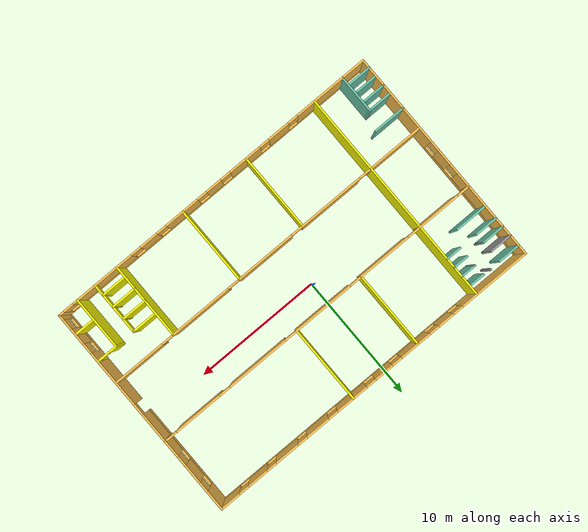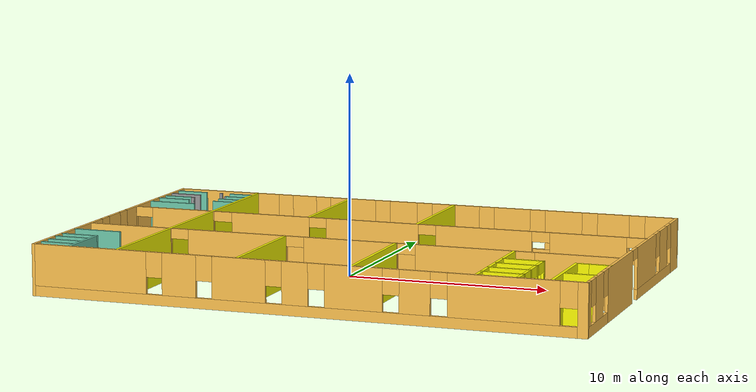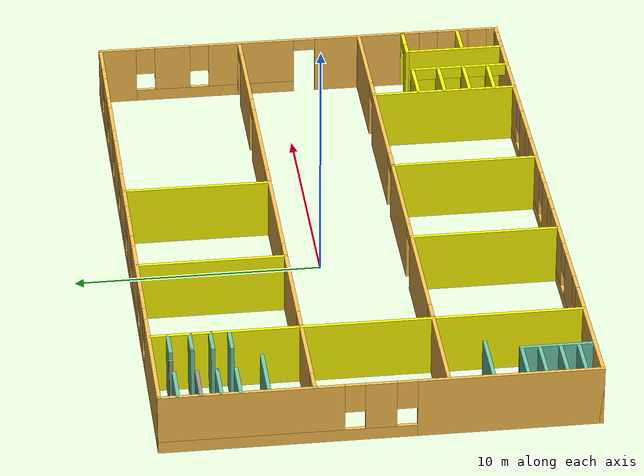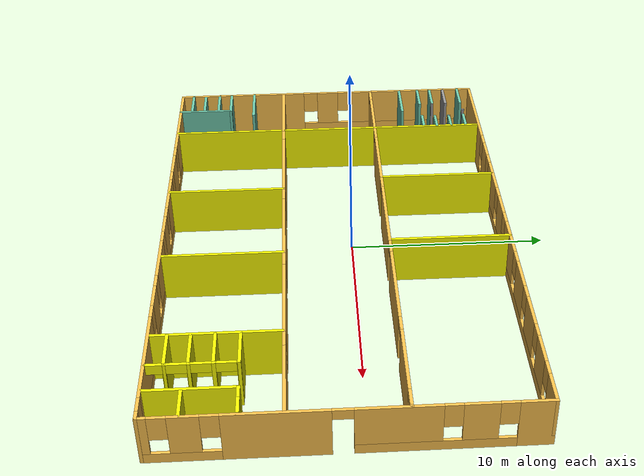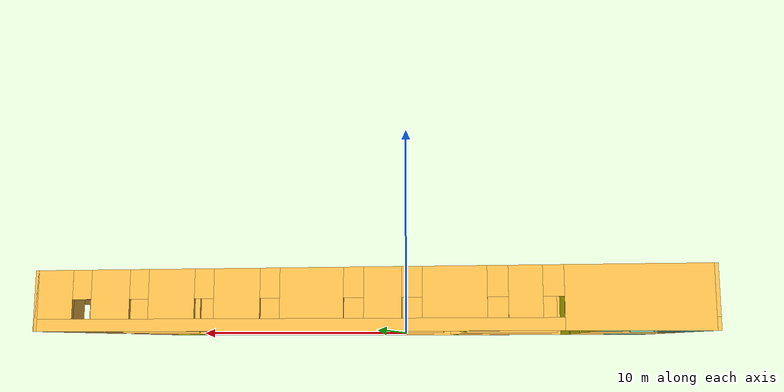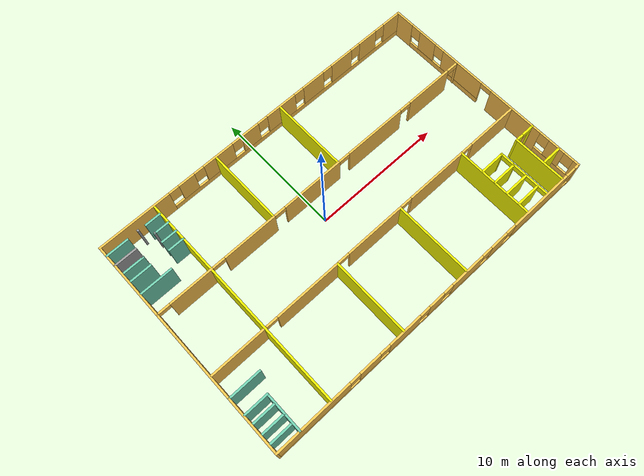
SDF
<?xml version='1.0'?>
<sdf version='1.6'>
  <model name='mybuilding'>
    <pose frame=''>1.04921 -0.845204 0 0 -0 0</pose>
    <link name='Wall_104'>
      <collision name='Wall_104_Collision'>
        <geometry>
          <box>
            <size>17.1 0.15 2.5</size>
          </box>
        </geometry>
        <pose frame=''>0 0 1.25 0 -0 0</pose>
      </collision>
      <visual name='Wall_104_Visual'>
        <pose frame=''>0 0 1.25 0 -0 0</pose>
        <geometry>
          <box>
            <size>17.1 0.15 2.5</size>
          </box>
        </geometry>
        <material>
          <script>
            <uri>file://media/materials/scripts/gazebo.material</uri>
            <name>Gazebo/Grey</name>
          </script>
          <ambient>1 1 0 1</ambient>
        </material>
        <meta>
          <layer>0</layer>
        </meta>
      </visual>
      <pose frame=''>-9.12987 -0.014892 0 0 0 -1.5708</pose>
    </link>
    <link name='Wall_106'>
      <collision name='Wall_106_Collision'>
        <geometry>
          <box>
            <size>2.5 0.15 2.5</size>
          </box>
        </geometry>
        <pose frame=''>0 0 1.25 0 -0 0</pose>
      </collision>
      <visual name='Wall_106_Visual'>
        <pose frame=''>0 0 1.25 0 -0 0</pose>
        <geometry>
          <box>
            <size>2.5 0.15 2.5</size>
          </box>
        </geometry>
        <material>
          <script>
            <uri>file://media/materials/scripts/gazebo.material</uri>
            <name>Gazebo/Grey</name>
          </script>
          <ambient>0.435294 0.796078 0.67451 1</ambient>
        </material>
        <meta>
          <layer>0</layer>
        </meta>
      </visual>
      <pose frame=''>-12.1433 4.3296 0 0 -0 0</pose>
    </link>
    <link name='Wall_111'>
      <collision name='Wall_111_Collision'>
        <geometry>
          <box>
            <size>2.5 0.15 2.5</size>
          </box>
        </geometry>
        <pose frame=''>0 0 1.25 0 -0 0</pose>
      </collision>
      <visual name='Wall_111_Visual'>
        <pose frame=''>0 0 1.25 0 -0 0</pose>
        <geometry>
          <box>
            <size>2.5 0.15 2.5</size>
          </box>
        </geometry>
        <material>
          <script>
            <uri>file://media/materials/scripts/gazebo.material</uri>
            <name>Gazebo/Grey</name>
          </script>
          <ambient>0.435294 0.796078 0.67451 1</ambient>
        </material>
        <meta>
          <layer>0</layer>
        </meta>
      </visual>
      <pose frame=''>-12.2145 -4.32806 0 0 -0 0</pose>
    </link>
    <link name='Wall_113'>
      <collision name='Wall_113_Collision'>
        <geometry>
          <box>
            <size>1.75 0.15 2.5</size>
          </box>
        </geometry>
        <pose frame=''>0 0 1.25 0 -0 0</pose>
      </collision>
      <visual name='Wall_113_Visual'>
        <pose frame=''>0 0 1.25 0 -0 0</pose>
        <geometry>
          <box>
            <size>1.75 0.15 2.5</size>
          </box>
        </geometry>
        <material>
          <script>
            <uri>file://media/materials/scripts/gazebo.material</uri>
            <name>Gazebo/Grey</name>
          </script>
          <ambient>0.435294 0.796078 0.67451 1</ambient>
        </material>
        <meta>
          <layer>0</layer>
        </meta>
      </visual>
      <pose frame=''>-12.5657 5.4207 0 0 -0 0</pose>
    </link>
    <link name='Wall_118'>
      <collision name='Wall_118_Collision'>
        <geometry>
          <box>
            <size>1.75 0.15 2.5</size>
          </box>
        </geometry>
        <pose frame=''>0 0 1.25 0 -0 0</pose>
      </collision>
      <visual name='Wall_118_Visual'>
        <pose frame=''>0 0 1.25 0 -0 0</pose>
        <geometry>
          <box>
            <size>1.75 0.15 2.5</size>
          </box>
        </geometry>
        <material>
          <script>
            <uri>file://media/materials/scripts/gazebo.material</uri>
            <name>Gazebo/Grey</name>
          </script>
          <ambient>1 1 1 1</ambient>
        </material>
        <meta>
          <layer>0</layer>
        </meta>
      </visual>
      <pose frame=''>-12.591 6.93726 0 0 -0 0</pose>
    </link>
    <link name='Wall_122'>
      <collision name='Wall_122_Collision'>
        <geometry>
          <box>
            <size>1.75 0.15 2.5</size>
          </box>
        </geometry>
        <pose frame=''>0 0 1.25 0 -0 0</pose>
      </collision>
      <visual name='Wall_122_Visual'>
        <pose frame=''>0 0 1.25 0 -0 0</pose>
        <geometry>
          <box>
            <size>1.75 0.15 2.5</size>
          </box>
        </geometry>
        <material>
          <script>
            <uri>file://media/materials/scripts/gazebo.material</uri>
            <name>Gazebo/Grey</name>
          </script>
          <ambient>0.435294 0.796078 0.67451 1</ambient>
        </material>
        <meta>
          <layer>0</layer>
        </meta>
      </visual>
      <pose frame=''>-12.591 7.81489 0 0 -0 0</pose>
    </link>
    <link name='Wall_124'>
      <collision name='Wall_124_Collision'>
        <geometry>
          <box>
            <size>1.75 0.15 2.5</size>
          </box>
        </geometry>
        <pose frame=''>0 0 1.25 0 -0 0</pose>
      </collision>
      <visual name='Wall_124_Visual'>
        <pose frame=''>0 0 1.25 0 -0 0</pose>
        <geometry>
          <box>
            <size>1.75 0.15 2.5</size>
          </box>
        </geometry>
        <material>
          <script>
            <uri>file://media/materials/scripts/gazebo.material</uri>
            <name>Gazebo/Grey</name>
          </script>
          <ambient>0.435294 0.796078 0.67451 1</ambient>
        </material>
        <meta>
          <layer>0</layer>
        </meta>
      </visual>
      <pose frame=''>-12.591 6.15451 0 0 -0 0</pose>
    </link>
    <link name='Wall_125'>
      <collision name='Wall_125_Collision'>
        <geometry>
          <box>
            <size>0.16 0.15 2.5</size>
          </box>
        </geometry>
        <pose frame=''>0 0 1.25 0 -0 0</pose>
      </collision>
      <visual name='Wall_125_Visual'>
        <pose frame=''>0 0 1.25 0 -0 0</pose>
        <geometry>
          <box>
            <size>0.16 0.15 2.5</size>
          </box>
        </geometry>
        <material>
          <script>
            <uri>file://media/materials/scripts/gazebo.material</uri>
            <name>Gazebo/Grey</name>
          </script>
          <ambient>0 0 0 0</ambient>
        </material>
        <meta>
          <layer>0</layer>
        </meta>
      </visual>
      <pose frame=''>-11.786 6.15451 0 0 -0 0</pose>
    </link>
    <link name='Wall_128'>
      <collision name='Wall_128_Collision'>
        <geometry>
          <box>
            <size>1.25 0.15 2.5</size>
          </box>
        </geometry>
        <pose frame=''>0 0 1.25 0 -0 0</pose>
      </collision>
      <visual name='Wall_128_Visual'>
        <pose frame=''>0 0 1.25 0 -0 0</pose>
        <geometry>
          <box>
            <size>1.25 0.15 2.5</size>
          </box>
        </geometry>
        <material>
          <script>
            <uri>file://media/materials/scripts/gazebo.material</uri>
            <name>Gazebo/Grey</name>
          </script>
          <ambient>0.435294 0.796078 0.67451 1</ambient>
        </material>
        <meta>
          <layer>0</layer>
        </meta>
      </visual>
      <pose frame=''>-9.76007 7.80847 0 0 -0 3.14159</pose>
    </link>
    <link name='Wall_130'>
      <collision name='Wall_130_Collision'>
        <geometry>
          <box>
            <size>1.25 0.15 2.5</size>
          </box>
        </geometry>
        <pose frame=''>0 0 1.25 0 -0 0</pose>
      </collision>
      <visual name='Wall_130_Visual'>
        <pose frame=''>0 0 1.25 0 -0 0</pose>
        <geometry>
          <box>
            <size>1.25 0.15 2.5</size>
          </box>
        </geometry>
        <material>
          <script>
            <uri>file://media/materials/scripts/gazebo.material</uri>
            <name>Gazebo/Grey</name>
          </script>
          <ambient>0.435294 0.796078 0.67451 1</ambient>
        </material>
        <meta>
          <layer>0</layer>
        </meta>
      </visual>
      <pose frame=''>-9.71164 6.96281 0 0 -0 3.14159</pose>
    </link>
    <link name='Wall_131'>
      <collision name='Wall_131_Collision'>
        <geometry>
          <box>
            <size>0.16 0.15 2.5</size>
          </box>
        </geometry>
        <pose frame=''>0 0 1.25 0 -0 0</pose>
      </collision>
      <visual name='Wall_131_Visual'>
        <pose frame=''>0 0 1.25 0 -0 0</pose>
        <geometry>
          <box>
            <size>0.16 0.15 2.5</size>
          </box>
        </geometry>
        <material>
          <script>
            <uri>file://media/materials/scripts/gazebo.material</uri>
            <name>Gazebo/Grey</name>
          </script>
          <ambient>0 0 0 0</ambient>
        </material>
        <meta>
          <layer>0</layer>
        </meta>
      </visual>
      <pose frame=''>-10.2566 6.96281 0 0 -0 0</pose>
    </link>
    <link name='Wall_132'>
      <collision name='Wall_132_Collision'>
        <geometry>
          <box>
            <size>1.25 0.15 2.5</size>
          </box>
        </geometry>
        <pose frame=''>0 0 1.25 0 -0 0</pose>
      </collision>
      <visual name='Wall_132_Visual'>
        <pose frame=''>0 0 1.25 0 -0 0</pose>
        <geometry>
          <box>
            <size>1.25 0.15 2.5</size>
          </box>
        </geometry>
        <material>
          <script>
            <uri>file://media/materials/scripts/gazebo.material</uri>
            <name>Gazebo/Grey</name>
          </script>
          <ambient>0.435294 0.796078 0.67451 1</ambient>
        </material>
        <meta>
          <layer>0</layer>
        </meta>
      </visual>
      <pose frame=''>-9.70141 6.15841 0 0 -0 3.14159</pose>
    </link>
    <link name='Wall_134'>
      <collision name='Wall_134_Collision'>
        <geometry>
          <box>
            <size>1.25 0.15 2.5</size>
          </box>
        </geometry>
        <pose frame=''>0 0 1.25 0 -0 0</pose>
      </collision>
      <visual name='Wall_134_Visual'>
        <pose frame=''>0 0 1.25 0 -0 0</pose>
        <geometry>
          <box>
            <size>1.25 0.15 2.5</size>
          </box>
        </geometry>
        <material>
          <script>
            <uri>file://media/materials/scripts/gazebo.material</uri>
            <name>Gazebo/Grey</name>
          </script>
          <ambient>0.435294 0.796078 0.67451 1</ambient>
        </material>
        <meta>
          <layer>0</layer>
        </meta>
      </visual>
      <pose frame=''>-9.7135 5.41701 0 0 -0 3.14159</pose>
    </link>
    <link name='Wall_139'>
      <collision name='Wall_139_Collision'>
        <geometry>
          <box>
            <size>3 0.15 2.5</size>
          </box>
        </geometry>
        <pose frame=''>0 0 1.25 0 -0 0</pose>
      </collision>
      <visual name='Wall_139_Visual'>
        <pose frame=''>0 0 1.25 0 -0 0</pose>
        <geometry>
          <box>
            <size>3 0.15 2.5</size>
          </box>
        </geometry>
        <material>
          <script>
            <uri>file://media/materials/scripts/gazebo.material</uri>
            <name>Gazebo/Grey</name>
          </script>
          <ambient>0.435294 0.796078 0.67451 1</ambient>
        </material>
        <meta>
          <layer>0</layer>
        </meta>
      </visual>
      <pose frame=''>-11.6 -7.09333 0 0 -0 1.5708</pose>
    </link>
    <link name='Wall_140'>
      <collision name='Wall_140_Collision'>
        <geometry>
          <box>
            <size>1.9 0.15 2.5</size>
          </box>
        </geometry>
        <pose frame=''>0 0 1.25 0 -0 0</pose>
      </collision>
      <visual name='Wall_140_Visual'>
        <pose frame=''>0 0 1.25 0 -0 0</pose>
        <geometry>
          <box>
            <size>1.9 0.15 2.5</size>
          </box>
        </geometry>
        <material>
          <script>
            <uri>file://media/materials/scripts/gazebo.material</uri>
            <name>Gazebo/Grey</name>
          </script>
          <ambient>0.435294 0.796078 0.67451 1</ambient>
        </material>
        <meta>
          <layer>0</layer>
        </meta>
      </visual>
      <pose frame=''>-12.475 -5.66833 0 0 -0 3.14159</pose>
    </link>
    <link name='Wall_142'>
      <collision name='Wall_142_Collision'>
        <geometry>
          <box>
            <size>1.75 0.15 2.5</size>
          </box>
        </geometry>
        <pose frame=''>0 0 1.25 0 -0 0</pose>
      </collision>
      <visual name='Wall_142_Visual'>
        <pose frame=''>0 0 1.25 0 -0 0</pose>
        <geometry>
          <box>
            <size>1.75 0.15 2.5</size>
          </box>
        </geometry>
        <material>
          <script>
            <uri>file://media/materials/scripts/gazebo.material</uri>
            <name>Gazebo/Grey</name>
          </script>
          <ambient>0.435294 0.796078 0.67451 1</ambient>
        </material>
        <meta>
          <layer>0</layer>
        </meta>
      </visual>
      <pose frame=''>-12.4841 -7.19003 0 0 -0 0</pose>
    </link>
    <link name='Wall_144'>
      <collision name='Wall_144_Collision'>
        <geometry>
          <box>
            <size>1.8 0.15 2.5</size>
          </box>
        </geometry>
        <pose frame=''>0 0 1.25 0 -0 0</pose>
      </collision>
      <visual name='Wall_144_Visual'>
        <pose frame=''>0 0 1.25 0 -0 0</pose>
        <geometry>
          <box>
            <size>1.8 0.15 2.5</size>
          </box>
        </geometry>
        <material>
          <script>
            <uri>file://media/materials/scripts/gazebo.material</uri>
            <name>Gazebo/Grey</name>
          </script>
          <ambient>0.435294 0.796078 0.67451 1</ambient>
        </material>
        <meta>
          <layer>0</layer>
        </meta>
      </visual>
      <pose frame=''>-12.5407 -6.37701 0 0 -0 0</pose>
    </link>
    <link name='Wall_147'>
      <collision name='Wall_147_Collision'>
        <geometry>
          <box>
            <size>1.8 0.15 2.5</size>
          </box>
        </geometry>
        <pose frame=''>0 0 1.25 0 -0 0</pose>
      </collision>
      <visual name='Wall_147_Visual'>
        <pose frame=''>0 0 1.25 0 -0 0</pose>
        <geometry>
          <box>
            <size>1.8 0.15 2.5</size>
          </box>
        </geometry>
        <material>
          <script>
            <uri>file://media/materials/scripts/gazebo.material</uri>
            <name>Gazebo/Grey</name>
          </script>
          <ambient>0.435294 0.796078 0.67451 1</ambient>
        </material>
        <meta>
          <layer>0</layer>
        </meta>
      </visual>
      <pose frame=''>-12.5758 -7.90564 0 0 -0 0</pose>
    </link>
    <link name='Wall_149'>
      <collision name='Wall_149_Collision'>
        <geometry>
          <box>
            <size>6 0.15 2.5</size>
          </box>
        </geometry>
        <pose frame=''>0 0 1.25 0 -0 0</pose>
      </collision>
      <visual name='Wall_149_Visual'>
        <pose frame=''>0 0 1.25 0 -0 0</pose>
        <geometry>
          <box>
            <size>6 0.15 2.5</size>
          </box>
        </geometry>
        <material>
          <script>
            <uri>file://media/materials/scripts/gazebo.material</uri>
            <name>Gazebo/Grey</name>
          </script>
          <ambient>1 1 0 1</ambient>
        </material>
        <meta>
          <layer>0</layer>
        </meta>
      </visual>
      <pose frame=''>1.80042 5.59279 0 0 0 -1.5708</pose>
    </link>
    <link name='Wall_151'>
      <collision name='Wall_151_Collision'>
        <geometry>
          <box>
            <size>6 0.15 2.5</size>
          </box>
        </geometry>
        <pose frame=''>0 0 1.25 0 -0 0</pose>
      </collision>
      <visual name='Wall_151_Visual'>
        <pose frame=''>0 0 1.25 0 -0 0</pose>
        <geometry>
          <box>
            <size>6 0.15 2.5</size>
          </box>
        </geometry>
        <material>
          <script>
            <uri>file://media/materials/scripts/gazebo.material</uri>
            <name>Gazebo/Grey</name>
          </script>
          <ambient>1 1 0 1</ambient>
        </material>
        <meta>
          <layer>0</layer>
        </meta>
      </visual>
      <pose frame=''>-3.91292 5.55304 0 0 0 -1.5708</pose>
    </link>
    <link name='Wall_154'>
      <collision name='Wall_154_Collision'>
        <geometry>
          <box>
            <size>6 0.15 2.5</size>
          </box>
        </geometry>
        <pose frame=''>0 0 1.25 0 -0 0</pose>
      </collision>
      <visual name='Wall_154_Visual'>
        <pose frame=''>0 0 1.25 0 -0 0</pose>
        <geometry>
          <box>
            <size>6 0.15 2.5</size>
          </box>
        </geometry>
        <material>
          <script>
            <uri>file://media/materials/scripts/gazebo.material</uri>
            <name>Gazebo/Grey</name>
          </script>
          <ambient>1 1 0 1</ambient>
        </material>
        <meta>
          <layer>0</layer>
        </meta>
      </visual>
      <pose frame=''>2.51252 -5.57355 0 0 0 -1.5708</pose>
    </link>
    <link name='Wall_156'>
      <collision name='Wall_156_Collision'>
        <geometry>
          <box>
            <size>6 0.15 2.5</size>
          </box>
        </geometry>
        <pose frame=''>0 0 1.25 0 -0 0</pose>
      </collision>
      <visual name='Wall_156_Visual'>
        <pose frame=''>0 0 1.25 0 -0 0</pose>
        <geometry>
          <box>
            <size>6 0.15 2.5</size>
          </box>
        </geometry>
        <material>
          <script>
            <uri>file://media/materials/scripts/gazebo.material</uri>
            <name>Gazebo/Grey</name>
          </script>
          <ambient>1 1 0 1</ambient>
        </material>
        <meta>
          <layer>0</layer>
        </meta>
      </visual>
      <pose frame=''>-3.08532 -5.54983 0 0 0 -1.5708</pose>
    </link>
    <link name='Wall_158'>
      <collision name='Wall_158_Collision'>
        <geometry>
          <box>
            <size>6 0.15 2.5</size>
          </box>
        </geometry>
        <pose frame=''>0 0 1.25 0 -0 0</pose>
      </collision>
      <visual name='Wall_158_Visual'>
        <pose frame=''>0 0 1.25 0 -0 0</pose>
        <geometry>
          <box>
            <size>6 0.15 2.5</size>
          </box>
        </geometry>
        <material>
          <script>
            <uri>file://media/materials/scripts/gazebo.material</uri>
            <name>Gazebo/Grey</name>
          </script>
          <ambient>1 1 0 1</ambient>
        </material>
        <meta>
          <layer>0</layer>
        </meta>
      </visual>
      <pose frame=''>8.34754 -5.57355 0 0 0 -1.5708</pose>
    </link>
    <link name='Wall_162'>
      <collision name='Wall_162_Collision'>
        <geometry>
          <box>
            <size>2 0.15 2.5</size>
          </box>
        </geometry>
        <pose frame=''>0 0 1.25 0 -0 0</pose>
      </collision>
      <visual name='Wall_162_Visual'>
        <pose frame=''>0 0 1.25 0 -0 0</pose>
        <geometry>
          <box>
            <size>2 0.15 2.5</size>
          </box>
        </geometry>
        <material>
          <script>
            <uri>file://media/materials/scripts/gazebo.material</uri>
            <name>Gazebo/Grey</name>
          </script>
          <ambient>1 1 0 1</ambient>
        </material>
        <meta>
          <layer>0</layer>
        </meta>
      </visual>
      <pose frame=''>9.34295 -4.49272 0 0 0 -8.3e-05</pose>
    </link>
    <link name='Wall_163'>
      <pose frame=''>10.2678 -6.5178 0 0 0 -1.5708</pose>
      <visual name='Wall_163_Visual_0'>
        <pose frame=''>-2.0133 0 1.25 0 -0 0</pose>
        <geometry>
          <box>
            <size>0.173407 0.15 2.5</size>
          </box>
        </geometry>
        <material>
          <script>
            <uri>file://media/materials/scripts/gazebo.material</uri>
            <name>Gazebo/Grey</name>
          </script>
          <ambient>1 1 0 1</ambient>
        </material>
        <meta>
          <layer>0</layer>
        </meta>
      </visual>
      <collision name='Wall_163_Collision_0'>
        <geometry>
          <box>
            <size>0.173407 0.15 2.5</size>
          </box>
        </geometry>
        <pose frame=''>-2.0133 0 1.25 0 -0 0</pose>
      </collision>
      <visual name='Wall_163_Visual_1'>
        <pose frame=''>-0.937243 0 1.25 0 -0 0</pose>
        <geometry>
          <box>
            <size>0.1787 0.15 2.5</size>
          </box>
        </geometry>
        <material>
          <script>
            <uri>file://media/materials/scripts/gazebo.material</uri>
            <name>Gazebo/Grey</name>
          </script>
          <ambient>1 1 0 1</ambient>
        </material>
        <meta>
          <layer>0</layer>
        </meta>
      </visual>
      <collision name='Wall_163_Collision_1'>
        <geometry>
          <box>
            <size>0.1787 0.15 2.5</size>
          </box>
        </geometry>
        <pose frame=''>-0.937243 0 1.25 0 -0 0</pose>
      </collision>
      <visual name='Wall_163_Visual_2'>
        <pose frame=''>0.125594 0 1.25 0 -0 0</pose>
        <geometry>
          <box>
            <size>0.146974 0.15 2.5</size>
          </box>
        </geometry>
        <material>
          <script>
            <uri>file://media/materials/scripts/gazebo.material</uri>
            <name>Gazebo/Grey</name>
          </script>
          <ambient>1 1 0 1</ambient>
        </material>
        <meta>
          <layer>0</layer>
        </meta>
      </visual>
      <collision name='Wall_163_Collision_2'>
        <geometry>
          <box>
            <size>0.146974 0.15 2.5</size>
          </box>
        </geometry>
        <pose frame=''>0.125594 0 1.25 0 -0 0</pose>
      </collision>
      <visual name='Wall_163_Visual_3'>
        <pose frame=''>1.16567 0 1.25 0 -0 0</pose>
        <geometry>
          <box>
            <size>0.133179 0.15 2.5</size>
          </box>
        </geometry>
        <material>
          <script>
            <uri>file://media/materials/scripts/gazebo.material</uri>
            <name>Gazebo/Grey</name>
          </script>
          <ambient>1 1 0 1</ambient>
        </material>
        <meta>
          <layer>0</layer>
        </meta>
      </visual>
      <collision name='Wall_163_Collision_3'>
        <geometry>
          <box>
            <size>0.133179 0.15 2.5</size>
          </box>
        </geometry>
        <pose frame=''>1.16567 0 1.25 0 -0 0</pose>
      </collision>
      <visual name='Wall_163_Visual_4'>
        <pose frame=''>-1.47659 0 2.25 0 -0 0</pose>
        <geometry>
          <box>
            <size>0.9 0.15 0.5</size>
          </box>
        </geometry>
        <material>
          <script>
            <uri>file://media/materials/scripts/gazebo.material</uri>
            <name>Gazebo/Grey</name>
          </script>
          <ambient>1 1 0 1</ambient>
        </material>
        <meta>
          <layer>0</layer>
        </meta>
      </visual>
      <collision name='Wall_163_Collision_4'>
        <geometry>
          <box>
            <size>0.9 0.15 0.5</size>
          </box>
        </geometry>
        <pose frame=''>-1.47659 0 2.25 0 -0 0</pose>
      </collision>
      <visual name='Wall_163_Visual_5'>
        <pose frame=''>-0.397893 0 2.25 0 -0 0</pose>
        <geometry>
          <box>
            <size>0.9 0.15 0.5</size>
          </box>
        </geometry>
        <material>
          <script>
            <uri>file://media/materials/scripts/gazebo.material</uri>
            <name>Gazebo/Grey</name>
          </script>
          <ambient>1 1 0 1</ambient>
        </material>
        <meta>
          <layer>0</layer>
        </meta>
      </visual>
      <collision name='Wall_163_Collision_5'>
        <geometry>
          <box>
            <size>0.9 0.15 0.5</size>
          </box>
        </geometry>
        <pose frame=''>-0.397893 0 2.25 0 -0 0</pose>
      </collision>
      <visual name='Wall_163_Visual_6'>
        <pose frame=''>0.649081 0 2.25 0 -0 0</pose>
        <geometry>
          <box>
            <size>0.9 0.15 0.5</size>
          </box>
        </geometry>
        <material>
          <script>
            <uri>file://media/materials/scripts/gazebo.material</uri>
            <name>Gazebo/Grey</name>
          </script>
          <ambient>1 1 0 1</ambient>
        </material>
        <meta>
          <layer>0</layer>
        </meta>
      </visual>
      <collision name='Wall_163_Collision_6'>
        <geometry>
          <box>
            <size>0.9 0.15 0.5</size>
          </box>
        </geometry>
        <pose frame=''>0.649081 0 2.25 0 -0 0</pose>
      </collision>
      <visual name='Wall_163_Visual_7'>
        <pose frame=''>1.66613 0 2.25 0 -0 0</pose>
        <geometry>
          <box>
            <size>0.867739 0.15 0.5</size>
          </box>
        </geometry>
        <material>
          <script>
            <uri>file://media/materials/scripts/gazebo.material</uri>
            <name>Gazebo/Grey</name>
          </script>
          <ambient>1 1 0 1</ambient>
        </material>
        <meta>
          <layer>0</layer>
        </meta>
      </visual>
      <collision name='Wall_163_Collision_7'>
        <geometry>
          <box>
            <size>0.867739 0.15 0.5</size>
          </box>
        </geometry>
        <pose frame=''>1.66613 0 2.25 0 -0 0</pose>
      </collision>
    </link>
    <link name='Wall_171'>
      <pose frame=''>12.6222 -4.4809 0 0 -0 3.14159</pose>
      <visual name='Wall_171_Visual_0'>
        <pose frame=''>-0.79093 0 1.25 0 -0 0</pose>
        <geometry>
          <box>
            <size>0.168139 0.15 2.5</size>
          </box>
        </geometry>
        <material>
          <script>
            <uri>file://media/materials/scripts/gazebo.material</uri>
            <name>Gazebo/Grey</name>
          </script>
          <ambient>1 1 0 1</ambient>
        </material>
        <meta>
          <layer>0</layer>
        </meta>
      </visual>
      <collision name='Wall_171_Collision_0'>
        <geometry>
          <box>
            <size>0.168139 0.15 2.5</size>
          </box>
        </geometry>
        <pose frame=''>-0.79093 0 1.25 0 -0 0</pose>
      </collision>
      <visual name='Wall_171_Visual_1'>
        <pose frame=''>0.53407 0 1.25 0 -0 0</pose>
        <geometry>
          <box>
            <size>0.681861 0.15 2.5</size>
          </box>
        </geometry>
        <material>
          <script>
            <uri>file://media/materials/scripts/gazebo.material</uri>
            <name>Gazebo/Grey</name>
          </script>
          <ambient>1 1 0 1</ambient>
        </material>
        <meta>
          <layer>0</layer>
        </meta>
      </visual>
      <collision name='Wall_171_Collision_1'>
        <geometry>
          <box>
            <size>0.681861 0.15 2.5</size>
          </box>
        </geometry>
        <pose frame=''>0.53407 0 1.25 0 -0 0</pose>
      </collision>
      <visual name='Wall_171_Visual_2'>
        <pose frame=''>-0.256861 0 2.25 0 -0 0</pose>
        <geometry>
          <box>
            <size>0.9 0.15 0.5</size>
          </box>
        </geometry>
        <material>
          <script>
            <uri>file://media/materials/scripts/gazebo.material</uri>
            <name>Gazebo/Grey</name>
          </script>
          <ambient>1 1 0 1</ambient>
        </material>
        <meta>
          <layer>0</layer>
        </meta>
      </visual>
      <collision name='Wall_171_Collision_2'>
        <geometry>
          <box>
            <size>0.9 0.15 0.5</size>
          </box>
        </geometry>
        <pose frame=''>-0.256861 0 2.25 0 -0 0</pose>
      </collision>
    </link>
    <link name='Wall_172'>
      <collision name='Wall_172_Collision'>
        <geometry>
          <box>
            <size>4.2 0.15 2.5</size>
          </box>
        </geometry>
        <pose frame=''>0 0 1.25 0 -0 0</pose>
      </collision>
      <visual name='Wall_172_Visual'>
        <pose frame=''>0 0 1.25 0 -0 0</pose>
        <geometry>
          <box>
            <size>4.2 0.15 2.5</size>
          </box>
        </geometry>
        <material>
          <script>
            <uri>file://media/materials/scripts/gazebo.material</uri>
            <name>Gazebo/Grey</name>
          </script>
          <ambient>1 1 0 1</ambient>
        </material>
        <meta>
          <layer>0</layer>
        </meta>
      </visual>
      <pose frame=''>11.8222 -6.5059 0 0 0 -1.5708</pose>
    </link>
    <link name='Wall_174'>
      <collision name='Wall_174_Collision'>
        <geometry>
          <box>
            <size>1.65 0.15 2.5</size>
          </box>
        </geometry>
        <pose frame=''>0 0 1.25 0 -0 0</pose>
      </collision>
      <visual name='Wall_174_Visual'>
        <pose frame=''>0 0 1.25 0 -0 0</pose>
        <geometry>
          <box>
            <size>1.65 0.15 2.5</size>
          </box>
        </geometry>
        <material>
          <script>
            <uri>file://media/materials/scripts/gazebo.material</uri>
            <name>Gazebo/Grey</name>
          </script>
          <ambient>1 1 0 1</ambient>
        </material>
        <meta>
          <layer>0</layer>
        </meta>
      </visual>
      <pose frame=''>12.6046 -6.85286 0 0 -0 0</pose>
    </link>
    <link name='Wall_176'>
      <collision name='Wall_176_Collision'>
        <geometry>
          <box>
            <size>2 0.15 2.5</size>
          </box>
        </geometry>
        <pose frame=''>0 0 1.25 0 -0 0</pose>
      </collision>
      <visual name='Wall_176_Visual'>
        <pose frame=''>0 0 1.25 0 -0 0</pose>
        <geometry>
          <box>
            <size>2 0.15 2.5</size>
          </box>
        </geometry>
        <material>
          <script>
            <uri>file://media/materials/scripts/gazebo.material</uri>
            <name>Gazebo/Grey</name>
          </script>
          <ambient>1 1 0 1</ambient>
        </material>
        <meta>
          <layer>0</layer>
        </meta>
      </visual>
      <pose frame=''>9.29387 -6.66723 0 0 -0 0</pose>
    </link>
    <link name='Wall_179'>
      <collision name='Wall_179_Collision'>
        <geometry>
          <box>
            <size>2 0.15 2.5</size>
          </box>
        </geometry>
        <pose frame=''>0 0 1.25 0 -0 0</pose>
      </collision>
      <visual name='Wall_179_Visual'>
        <pose frame=''>0 0 1.25 0 -0 0</pose>
        <geometry>
          <box>
            <size>2 0.15 2.5</size>
          </box>
        </geometry>
        <material>
          <script>
            <uri>file://media/materials/scripts/gazebo.material</uri>
            <name>Gazebo/Grey</name>
          </script>
          <ambient>1 1 0 1</ambient>
        </material>
        <meta>
          <layer>0</layer>
        </meta>
      </visual>
      <pose frame=''>9.31988 -5.59469 0 0 -0 0</pose>
    </link>
    <link name='Wall_182'>
      <collision name='Wall_182_Collision'>
        <geometry>
          <box>
            <size>2 0.15 2.5</size>
          </box>
        </geometry>
        <pose frame=''>0 0 1.25 0 -0 0</pose>
      </collision>
      <visual name='Wall_182_Visual'>
        <pose frame=''>0 0 1.25 0 -0 0</pose>
        <geometry>
          <box>
            <size>2 0.15 2.5</size>
          </box>
        </geometry>
        <material>
          <script>
            <uri>file://media/materials/scripts/gazebo.material</uri>
            <name>Gazebo/Grey</name>
          </script>
          <ambient>1 1 0 1</ambient>
        </material>
        <meta>
          <layer>0</layer>
        </meta>
      </visual>
      <pose frame=''>9.29143 -7.70507 0 0 -0 0</pose>
    </link>
    <link name='Wall_185'>
      <collision name='Wall_185_Collision'>
        <geometry>
          <box>
            <size>0.15 0.15 2.5</size>
          </box>
        </geometry>
        <pose frame=''>0 0 1.25 0 -0 0</pose>
      </collision>
      <visual name='Wall_185_Visual'>
        <pose frame=''>0 0 1.25 0 -0 0</pose>
        <geometry>
          <box>
            <size>0.15 0.15 2.5</size>
          </box>
        </geometry>
        <material>
          <script>
            <uri>file://media/materials/scripts/gazebo.material</uri>
            <name>Gazebo/Grey</name>
          </script>
          <ambient>1 1 1 1</ambient>
        </material>
        <meta>
          <layer>0</layer>
        </meta>
      </visual>
      <pose frame=''>-10.9249 7.85699 0 0 -0 0</pose>
    </link>
    <link name='Wall_89'>
      <pose frame=''>-13.425 0 0 0 -0 1.5708</pose>
      <visual name='Wall_89_Visual_0'>
        <pose frame=''>-5.00389 0 1.25 0 -0 0</pose>
        <geometry>
          <box>
            <size>7.24221 0.15 2.5</size>
          </box>
        </geometry>
        <material>
          <script>
            <uri>file://media/materials/scripts/gazebo.material</uri>
            <name>Gazebo/Grey</name>
          </script>
          <ambient>1 0.764706 0.305882 1</ambient>
        </material>
        <meta>
          <layer>0</layer>
        </meta>
      </visual>
      <collision name='Wall_89_Collision_0'>
        <geometry>
          <box>
            <size>7.24221 0.15 2.5</size>
          </box>
        </geometry>
        <pose frame=''>-5.00389 0 1.25 0 -0 0</pose>
      </collision>
      <visual name='Wall_89_Visual_1'>
        <pose frame=''>3.62111 0 0.25 0 -0 0</pose>
        <geometry>
          <box>
            <size>10.0078 0.15 0.5</size>
          </box>
        </geometry>
        <material>
          <script>
            <uri>file://media/materials/scripts/gazebo.material</uri>
            <name>Gazebo/Grey</name>
          </script>
          <ambient>1 0.764706 0.305882 1</ambient>
        </material>
        <meta>
          <layer>0</layer>
        </meta>
      </visual>
      <collision name='Wall_89_Collision_1'>
        <geometry>
          <box>
            <size>10.0078 0.15 0.5</size>
          </box>
        </geometry>
        <pose frame=''>3.62111 0 0.25 0 -0 0</pose>
      </collision>
      <visual name='Wall_89_Visual_2'>
        <pose frame=''>0.026482 0 1.5 0 -0 0</pose>
        <geometry>
          <box>
            <size>1.21854 0.15 2</size>
          </box>
        </geometry>
        <material>
          <script>
            <uri>file://media/materials/scripts/gazebo.material</uri>
            <name>Gazebo/Grey</name>
          </script>
          <ambient>1 0.764706 0.305882 1</ambient>
        </material>
        <meta>
          <layer>0</layer>
        </meta>
      </visual>
      <collision name='Wall_89_Collision_2'>
        <geometry>
          <box>
            <size>1.21854 0.15 2</size>
          </box>
        </geometry>
        <pose frame=''>0.026482 0 1.5 0 -0 0</pose>
      </collision>
      <visual name='Wall_89_Visual_3'>
        <pose frame=''>5.03038 0 1.5 0 -0 0</pose>
        <geometry>
          <box>
            <size>7.18925 0.15 2</size>
          </box>
        </geometry>
        <material>
          <script>
            <uri>file://media/materials/scripts/gazebo.material</uri>
            <name>Gazebo/Grey</name>
          </script>
          <ambient>1 0.764706 0.305882 1</ambient>
        </material>
        <meta>
          <layer>0</layer>
        </meta>
      </visual>
      <collision name='Wall_89_Collision_3'>
        <geometry>
          <box>
            <size>7.18925 0.15 2</size>
          </box>
        </geometry>
        <pose frame=''>5.03038 0 1.5 0 -0 0</pose>
      </collision>
      <visual name='Wall_89_Visual_4'>
        <pose frame=''>-0.982788 0 1.9 0 -0 0</pose>
        <geometry>
          <box>
            <size>0.8 0.15 1.2</size>
          </box>
        </geometry>
        <material>
          <script>
            <uri>file://media/materials/scripts/gazebo.material</uri>
            <name>Gazebo/Grey</name>
          </script>
          <ambient>1 0.764706 0.305882 1</ambient>
        </material>
        <meta>
          <layer>0</layer>
        </meta>
      </visual>
      <collision name='Wall_89_Collision_4'>
        <geometry>
          <box>
            <size>0.8 0.15 1.2</size>
          </box>
        </geometry>
        <pose frame=''>-0.982788 0 1.9 0 -0 0</pose>
      </collision>
      <visual name='Wall_89_Visual_5'>
        <pose frame=''>1.03575 0 1.9 0 -0 0</pose>
        <geometry>
          <box>
            <size>0.8 0.15 1.2</size>
          </box>
        </geometry>
        <material>
          <script>
            <uri>file://media/materials/scripts/gazebo.material</uri>
            <name>Gazebo/Grey</name>
          </script>
          <ambient>1 0.764706 0.305882 1</ambient>
        </material>
        <meta>
          <layer>0</layer>
        </meta>
      </visual>
      <collision name='Wall_89_Collision_5'>
        <geometry>
          <box>
            <size>0.8 0.15 1.2</size>
          </box>
        </geometry>
        <pose frame=''>1.03575 0 1.9 0 -0 0</pose>
      </collision>
    </link>
    <link name='Wall_90'>
      <pose frame=''>0 8.55 0 0 -0 0</pose>
      <visual name='Wall_90_Visual_0'>
        <pose frame=''>-10.6849 0 1.25 0 -0 0</pose>
        <geometry>
          <box>
            <size>5.63012 0.15 2.5</size>
          </box>
        </geometry>
        <material>
          <script>
            <uri>file://media/materials/scripts/gazebo.material</uri>
            <name>Gazebo/Grey</name>
          </script>
          <ambient>1 0.764706 0.305882 1</ambient>
        </material>
        <meta>
          <layer>0</layer>
        </meta>
      </visual>
      <collision name='Wall_90_Collision_0'>
        <geometry>
          <box>
            <size>5.63012 0.15 2.5</size>
          </box>
        </geometry>
        <pose frame=''>-10.6849 0 1.25 0 -0 0</pose>
      </collision>
      <visual name='Wall_90_Visual_1'>
        <pose frame=''>2.81506 0 0.25 0 -0 0</pose>
        <geometry>
          <box>
            <size>21.3699 0.15 0.5</size>
          </box>
        </geometry>
        <material>
          <script>
            <uri>file://media/materials/scripts/gazebo.material</uri>
            <name>Gazebo/Grey</name>
          </script>
          <ambient>1 0.764706 0.305882 1</ambient>
        </material>
        <meta>
          <layer>0</layer>
        </meta>
      </visual>
      <collision name='Wall_90_Collision_1'>
        <geometry>
          <box>
            <size>21.3699 0.15 0.5</size>
          </box>
        </geometry>
        <pose frame=''>2.81506 0 0.25 0 -0 0</pose>
      </collision>
      <visual name='Wall_90_Visual_2'>
        <pose frame=''>-6.41969 0 1.5 0 -0 0</pose>
        <geometry>
          <box>
            <size>1.30037 0.15 2</size>
          </box>
        </geometry>
        <material>
          <script>
            <uri>file://media/materials/scripts/gazebo.material</uri>
            <name>Gazebo/Grey</name>
          </script>
          <ambient>1 0.764706 0.305882 1</ambient>
        </material>
        <meta>
          <layer>0</layer>
        </meta>
      </visual>
      <collision name='Wall_90_Collision_2'>
        <geometry>
          <box>
            <size>1.30037 0.15 2</size>
          </box>
        </geometry>
        <pose frame=''>-6.41969 0 1.5 0 -0 0</pose>
      </collision>
      <visual name='Wall_90_Visual_3'>
        <pose frame=''>-3.71922 0 1.5 0 -0 0</pose>
        <geometry>
          <box>
            <size>2.50059 0.15 2</size>
          </box>
        </geometry>
        <material>
          <script>
            <uri>file://media/materials/scripts/gazebo.material</uri>
            <name>Gazebo/Grey</name>
          </script>
          <ambient>1 0.764706 0.305882 1</ambient>
        </material>
        <meta>
          <layer>0</layer>
        </meta>
      </visual>
      <collision name='Wall_90_Collision_3'>
        <geometry>
          <box>
            <size>2.50059 0.15 2</size>
          </box>
        </geometry>
        <pose frame=''>-3.71922 0 1.5 0 -0 0</pose>
      </collision>
      <visual name='Wall_90_Visual_4'>
        <pose frame=''>-0.923265 0 1.5 0 -0 0</pose>
        <geometry>
          <box>
            <size>1.49131 0.15 2</size>
          </box>
        </geometry>
        <material>
          <script>
            <uri>file://media/materials/scripts/gazebo.material</uri>
            <name>Gazebo/Grey</name>
          </script>
          <ambient>1 0.764706 0.305882 1</ambient>
        </material>
        <meta>
          <layer>0</layer>
        </meta>
      </visual>
      <collision name='Wall_90_Collision_4'>
        <geometry>
          <box>
            <size>1.49131 0.15 2</size>
          </box>
        </geometry>
        <pose frame=''>-0.923265 0 1.5 0 -0 0</pose>
      </collision>
      <visual name='Wall_90_Visual_5'>
        <pose frame=''>1.90157 0 1.5 0 -0 0</pose>
        <geometry>
          <box>
            <size>2.55835 0.15 2</size>
          </box>
        </geometry>
        <material>
          <script>
            <uri>file://media/materials/scripts/gazebo.material</uri>
            <name>Gazebo/Grey</name>
          </script>
          <ambient>1 0.764706 0.305882 1</ambient>
        </material>
        <meta>
          <layer>0</layer>
        </meta>
      </visual>
      <collision name='Wall_90_Collision_5'>
        <geometry>
          <box>
            <size>2.55835 0.15 2</size>
          </box>
        </geometry>
        <pose frame=''>1.90157 0 1.5 0 -0 0</pose>
      </collision>
      <visual name='Wall_90_Visual_6'>
        <pose frame=''>4.92912 0 1.5 0 -0 0</pose>
        <geometry>
          <box>
            <size>1.89675 0.15 2</size>
          </box>
        </geometry>
        <material>
          <script>
            <uri>file://media/materials/scripts/gazebo.material</uri>
            <name>Gazebo/Grey</name>
          </script>
          <ambient>1 0.764706 0.305882 1</ambient>
        </material>
        <meta>
          <layer>0</layer>
        </meta>
      </visual>
      <collision name='Wall_90_Collision_6'>
        <geometry>
          <box>
            <size>1.89675 0.15 2</size>
          </box>
        </geometry>
        <pose frame=''>4.92912 0 1.5 0 -0 0</pose>
      </collision>
      <visual name='Wall_90_Visual_7'>
        <pose frame=''>7.64173 0 1.5 0 -0 0</pose>
        <geometry>
          <box>
            <size>1.92848 0.15 2</size>
          </box>
        </geometry>
        <material>
          <script>
            <uri>file://media/materials/scripts/gazebo.material</uri>
            <name>Gazebo/Grey</name>
          </script>
          <ambient>1 0.764706 0.305882 1</ambient>
        </material>
        <meta>
          <layer>0</layer>
        </meta>
      </visual>
      <collision name='Wall_90_Collision_7'>
        <geometry>
          <box>
            <size>1.92848 0.15 2</size>
          </box>
        </geometry>
        <pose frame=''>7.64173 0 1.5 0 -0 0</pose>
      </collision>
      <visual name='Wall_90_Visual_8'>
        <pose frame=''>10.2274 0 1.5 0 -0 0</pose>
        <geometry>
          <box>
            <size>1.64294 0.15 2</size>
          </box>
        </geometry>
        <material>
          <script>
            <uri>file://media/materials/scripts/gazebo.material</uri>
            <name>Gazebo/Grey</name>
          </script>
          <ambient>1 0.764706 0.305882 1</ambient>
        </material>
        <meta>
          <layer>0</layer>
        </meta>
      </visual>
      <collision name='Wall_90_Collision_8'>
        <geometry>
          <box>
            <size>1.64294 0.15 2</size>
          </box>
        </geometry>
        <pose frame=''>10.2274 0 1.5 0 -0 0</pose>
      </collision>
      <visual name='Wall_90_Visual_9'>
        <pose frame=''>12.6745 0 1.5 0 -0 0</pose>
        <geometry>
          <box>
            <size>1.65109 0.15 2</size>
          </box>
        </geometry>
        <material>
          <script>
            <uri>file://media/materials/scripts/gazebo.material</uri>
            <name>Gazebo/Grey</name>
          </script>
          <ambient>1 0.764706 0.305882 1</ambient>
        </material>
        <meta>
          <layer>0</layer>
        </meta>
      </visual>
      <collision name='Wall_90_Collision_9'>
        <geometry>
          <box>
            <size>1.65109 0.15 2</size>
          </box>
        </geometry>
        <pose frame=''>12.6745 0 1.5 0 -0 0</pose>
      </collision>
      <visual name='Wall_90_Visual_10'>
        <pose frame=''>-7.46988 0 1.9 0 -0 0</pose>
        <geometry>
          <box>
            <size>0.8 0.15 1.2</size>
          </box>
        </geometry>
        <material>
          <script>
            <uri>file://media/materials/scripts/gazebo.material</uri>
            <name>Gazebo/Grey</name>
          </script>
          <ambient>1 0.764706 0.305882 1</ambient>
        </material>
        <meta>
          <layer>0</layer>
        </meta>
      </visual>
      <collision name='Wall_90_Collision_10'>
        <geometry>
          <box>
            <size>0.8 0.15 1.2</size>
          </box>
        </geometry>
        <pose frame=''>-7.46988 0 1.9 0 -0 0</pose>
      </collision>
      <visual name='Wall_90_Visual_11'>
        <pose frame=''>-5.36951 0 1.9 0 -0 0</pose>
        <geometry>
          <box>
            <size>0.8 0.15 1.2</size>
          </box>
        </geometry>
        <material>
          <script>
            <uri>file://media/materials/scripts/gazebo.material</uri>
            <name>Gazebo/Grey</name>
          </script>
          <ambient>1 0.764706 0.305882 1</ambient>
        </material>
        <meta>
          <layer>0</layer>
        </meta>
      </visual>
      <collision name='Wall_90_Collision_11'>
        <geometry>
          <box>
            <size>0.8 0.15 1.2</size>
          </box>
        </geometry>
        <pose frame=''>-5.36951 0 1.9 0 -0 0</pose>
      </collision>
      <visual name='Wall_90_Visual_12'>
        <pose frame=''>-2.06892 0 1.9 0 -0 0</pose>
        <geometry>
          <box>
            <size>0.8 0.15 1.2</size>
          </box>
        </geometry>
        <material>
          <script>
            <uri>file://media/materials/scripts/gazebo.material</uri>
            <name>Gazebo/Grey</name>
          </script>
          <ambient>1 0.764706 0.305882 1</ambient>
        </material>
        <meta>
          <layer>0</layer>
        </meta>
      </visual>
      <collision name='Wall_90_Collision_12'>
        <geometry>
          <box>
            <size>0.8 0.15 1.2</size>
          </box>
        </geometry>
        <pose frame=''>-2.06892 0 1.9 0 -0 0</pose>
      </collision>
      <visual name='Wall_90_Visual_13'>
        <pose frame=''>0.222393 0 1.9 0 -0 0</pose>
        <geometry>
          <box>
            <size>0.8 0.15 1.2</size>
          </box>
        </geometry>
        <material>
          <script>
            <uri>file://media/materials/scripts/gazebo.material</uri>
            <name>Gazebo/Grey</name>
          </script>
          <ambient>1 0.764706 0.305882 1</ambient>
        </material>
        <meta>
          <layer>0</layer>
        </meta>
      </visual>
      <collision name='Wall_90_Collision_13'>
        <geometry>
          <box>
            <size>0.8 0.15 1.2</size>
          </box>
        </geometry>
        <pose frame=''>0.222393 0 1.9 0 -0 0</pose>
      </collision>
      <visual name='Wall_90_Visual_14'>
        <pose frame=''>3.58074 0 1.9 0 -0 0</pose>
        <geometry>
          <box>
            <size>0.8 0.15 1.2</size>
          </box>
        </geometry>
        <material>
          <script>
            <uri>file://media/materials/scripts/gazebo.material</uri>
            <name>Gazebo/Grey</name>
          </script>
          <ambient>1 0.764706 0.305882 1</ambient>
        </material>
        <meta>
          <layer>0</layer>
        </meta>
      </visual>
      <collision name='Wall_90_Collision_14'>
        <geometry>
          <box>
            <size>0.8 0.15 1.2</size>
          </box>
        </geometry>
        <pose frame=''>3.58074 0 1.9 0 -0 0</pose>
      </collision>
      <visual name='Wall_90_Visual_15'>
        <pose frame=''>6.27749 0 1.9 0 -0 0</pose>
        <geometry>
          <box>
            <size>0.8 0.15 1.2</size>
          </box>
        </geometry>
        <material>
          <script>
            <uri>file://media/materials/scripts/gazebo.material</uri>
            <name>Gazebo/Grey</name>
          </script>
          <ambient>1 0.764706 0.305882 1</ambient>
        </material>
        <meta>
          <layer>0</layer>
        </meta>
      </visual>
      <collision name='Wall_90_Collision_15'>
        <geometry>
          <box>
            <size>0.8 0.15 1.2</size>
          </box>
        </geometry>
        <pose frame=''>6.27749 0 1.9 0 -0 0</pose>
      </collision>
      <visual name='Wall_90_Visual_16'>
        <pose frame=''>9.00597 0 1.9 0 -0 0</pose>
        <geometry>
          <box>
            <size>0.8 0.15 1.2</size>
          </box>
        </geometry>
        <material>
          <script>
            <uri>file://media/materials/scripts/gazebo.material</uri>
            <name>Gazebo/Grey</name>
          </script>
          <ambient>1 0.764706 0.305882 1</ambient>
        </material>
        <meta>
          <layer>0</layer>
        </meta>
      </visual>
      <collision name='Wall_90_Collision_16'>
        <geometry>
          <box>
            <size>0.8 0.15 1.2</size>
          </box>
        </geometry>
        <pose frame=''>9.00597 0 1.9 0 -0 0</pose>
      </collision>
      <visual name='Wall_90_Visual_17'>
        <pose frame=''>11.4489 0 1.9 0 -0 0</pose>
        <geometry>
          <box>
            <size>0.8 0.15 1.2</size>
          </box>
        </geometry>
        <material>
          <script>
            <uri>file://media/materials/scripts/gazebo.material</uri>
            <name>Gazebo/Grey</name>
          </script>
          <ambient>1 0.764706 0.305882 1</ambient>
        </material>
        <meta>
          <layer>0</layer>
        </meta>
      </visual>
      <collision name='Wall_90_Collision_17'>
        <geometry>
          <box>
            <size>0.8 0.15 1.2</size>
          </box>
        </geometry>
        <pose frame=''>11.4489 0 1.9 0 -0 0</pose>
      </collision>
    </link>
    <link name='Wall_91'>
      <pose frame=''>13.425 0 0 0 0 -1.5708</pose>
      <visual name='Wall_91_Visual_0'>
        <pose frame=''>-7.82957 0 1.25 0 -0 0</pose>
        <geometry>
          <box>
            <size>1.59086 0.15 2.5</size>
          </box>
        </geometry>
        <material>
          <script>
            <uri>file://media/materials/scripts/gazebo.material</uri>
            <name>Gazebo/Grey</name>
          </script>
          <ambient>1 0.764706 0.305882 1</ambient>
        </material>
        <meta>
          <layer>0</layer>
        </meta>
      </visual>
      <collision name='Wall_91_Collision_0'>
        <geometry>
          <box>
            <size>1.59086 0.15 2.5</size>
          </box>
        </geometry>
        <pose frame=''>-7.82957 0 1.25 0 -0 0</pose>
      </collision>
      <visual name='Wall_91_Visual_1'>
        <pose frame=''>2.94053 0 1.25 0 -0 0</pose>
        <geometry>
          <box>
            <size>4.5435 0.15 2.5</size>
          </box>
        </geometry>
        <material>
          <script>
            <uri>file://media/materials/scripts/gazebo.material</uri>
            <name>Gazebo/Grey</name>
          </script>
          <ambient>1 0.764706 0.305882 1</ambient>
        </material>
        <meta>
          <layer>0</layer>
        </meta>
      </visual>
      <collision name='Wall_91_Collision_1'>
        <geometry>
          <box>
            <size>4.5435 0.15 2.5</size>
          </box>
        </geometry>
        <pose frame=''>2.94053 0 1.25 0 -0 0</pose>
      </collision>
      <visual name='Wall_91_Visual_2'>
        <pose frame=''>-3.63268 0 0.25 0 -0 0</pose>
        <geometry>
          <box>
            <size>6.80292 0.15 0.5</size>
          </box>
        </geometry>
        <material>
          <script>
            <uri>file://media/materials/scripts/gazebo.material</uri>
            <name>Gazebo/Grey</name>
          </script>
          <ambient>1 0.764706 0.305882 1</ambient>
        </material>
        <meta>
          <layer>0</layer>
        </meta>
      </visual>
      <collision name='Wall_91_Collision_2'>
        <geometry>
          <box>
            <size>6.80292 0.15 0.5</size>
          </box>
        </geometry>
        <pose frame=''>-3.63268 0 0.25 0 -0 0</pose>
      </collision>
      <visual name='Wall_91_Visual_3'>
        <pose frame=''>6.91864 0 0.25 0 -0 0</pose>
        <geometry>
          <box>
            <size>3.41272 0.15 0.5</size>
          </box>
        </geometry>
        <material>
          <script>
            <uri>file://media/materials/scripts/gazebo.material</uri>
            <name>Gazebo/Grey</name>
          </script>
          <ambient>1 0.764706 0.305882 1</ambient>
        </material>
        <meta>
          <layer>0</layer>
        </meta>
      </visual>
      <collision name='Wall_91_Collision_3'>
        <geometry>
          <box>
            <size>3.41272 0.15 0.5</size>
          </box>
        </geometry>
        <pose frame=''>6.91864 0 0.25 0 -0 0</pose>
      </collision>
      <visual name='Wall_91_Visual_4'>
        <pose frame=''>-5.47612 0 1.5 0 -0 0</pose>
        <geometry>
          <box>
            <size>1.51603 0.15 2</size>
          </box>
        </geometry>
        <material>
          <script>
            <uri>file://media/materials/scripts/gazebo.material</uri>
            <name>Gazebo/Grey</name>
          </script>
          <ambient>1 0.764706 0.305882 1</ambient>
        </material>
        <meta>
          <layer>0</layer>
        </meta>
      </visual>
      <collision name='Wall_91_Collision_4'>
        <geometry>
          <box>
            <size>1.51603 0.15 2</size>
          </box>
        </geometry>
        <pose frame=''>-5.47612 0 1.5 0 -0 0</pose>
      </collision>
      <visual name='Wall_91_Visual_5'>
        <pose frame=''>-2.07466 0 1.5 0 -0 0</pose>
        <geometry>
          <box>
            <size>3.68689 0.15 2</size>
          </box>
        </geometry>
        <material>
          <script>
            <uri>file://media/materials/scripts/gazebo.material</uri>
            <name>Gazebo/Grey</name>
          </script>
          <ambient>1 0.764706 0.305882 1</ambient>
        </material>
        <meta>
          <layer>0</layer>
        </meta>
      </visual>
      <collision name='Wall_91_Collision_5'>
        <geometry>
          <box>
            <size>3.68689 0.15 2</size>
          </box>
        </geometry>
        <pose frame=''>-2.07466 0 1.5 0 -0 0</pose>
      </collision>
      <visual name='Wall_91_Visual_6'>
        <pose frame=''>-2.07466 0 1.5 0 -0 0</pose>
        <geometry>
          <box>
            <size>3.68689 0.15 2</size>
          </box>
        </geometry>
        <material>
          <script>
            <uri>file://media/materials/scripts/gazebo.material</uri>
            <name>Gazebo/Grey</name>
          </script>
          <ambient>1 0.764706 0.305882 1</ambient>
        </material>
        <meta>
          <layer>0</layer>
        </meta>
      </visual>
      <collision name='Wall_91_Collision_6'>
        <geometry>
          <box>
            <size>3.68689 0.15 2</size>
          </box>
        </geometry>
        <pose frame=''>-2.07466 0 1.5 0 -0 0</pose>
      </collision>
      <visual name='Wall_91_Visual_7'>
        <pose frame=''>6.67512 0 1.5 0 -0 0</pose>
        <geometry>
          <box>
            <size>1.32567 0.15 2</size>
          </box>
        </geometry>
        <material>
          <script>
            <uri>file://media/materials/scripts/gazebo.material</uri>
            <name>Gazebo/Grey</name>
          </script>
          <ambient>1 0.764706 0.305882 1</ambient>
        </material>
        <meta>
          <layer>0</layer>
        </meta>
      </visual>
      <collision name='Wall_91_Collision_7'>
        <geometry>
          <box>
            <size>1.32567 0.15 2</size>
          </box>
        </geometry>
        <pose frame=''>6.67512 0 1.5 0 -0 0</pose>
      </collision>
      <visual name='Wall_91_Visual_8'>
        <pose frame=''>8.38148 0 1.5 0 -0 0</pose>
        <geometry>
          <box>
            <size>0.487047 0.15 2</size>
          </box>
        </geometry>
        <material>
          <script>
            <uri>file://media/materials/scripts/gazebo.material</uri>
            <name>Gazebo/Grey</name>
          </script>
          <ambient>1 0.764706 0.305882 1</ambient>
        </material>
        <meta>
          <layer>0</layer>
        </meta>
      </visual>
      <collision name='Wall_91_Collision_8'>
        <geometry>
          <box>
            <size>0.487047 0.15 2</size>
          </box>
        </geometry>
        <pose frame=''>8.38148 0 1.5 0 -0 0</pose>
      </collision>
      <visual name='Wall_91_Visual_9'>
        <pose frame=''>-6.63414 0 1.9 0 -0 0</pose>
        <geometry>
          <box>
            <size>0.8 0.15 1.2</size>
          </box>
        </geometry>
        <material>
          <script>
            <uri>file://media/materials/scripts/gazebo.material</uri>
            <name>Gazebo/Grey</name>
          </script>
          <ambient>1 0.764706 0.305882 1</ambient>
        </material>
        <meta>
          <layer>0</layer>
        </meta>
      </visual>
      <collision name='Wall_91_Collision_9'>
        <geometry>
          <box>
            <size>0.8 0.15 1.2</size>
          </box>
        </geometry>
        <pose frame=''>-6.63414 0 1.9 0 -0 0</pose>
      </collision>
      <visual name='Wall_91_Visual_10'>
        <pose frame=''>5.61228 0 1.9 0 -0 0</pose>
        <geometry>
          <box>
            <size>0.8 0.15 1.2</size>
          </box>
        </geometry>
        <material>
          <script>
            <uri>file://media/materials/scripts/gazebo.material</uri>
            <name>Gazebo/Grey</name>
          </script>
          <ambient>1 0.764706 0.305882 1</ambient>
        </material>
        <meta>
          <layer>0</layer>
        </meta>
      </visual>
      <collision name='Wall_91_Collision_10'>
        <geometry>
          <box>
            <size>0.8 0.15 1.2</size>
          </box>
        </geometry>
        <pose frame=''>5.61228 0 1.9 0 -0 0</pose>
      </collision>
      <visual name='Wall_91_Visual_11'>
        <pose frame=''>-4.31811 0 1.9 0 -0 0</pose>
        <geometry>
          <box>
            <size>0.8 0.15 1.2</size>
          </box>
        </geometry>
        <material>
          <script>
            <uri>file://media/materials/scripts/gazebo.material</uri>
            <name>Gazebo/Grey</name>
          </script>
          <ambient>1 0.764706 0.305882 1</ambient>
        </material>
        <meta>
          <layer>0</layer>
        </meta>
      </visual>
      <collision name='Wall_91_Collision_11'>
        <geometry>
          <box>
            <size>0.8 0.15 1.2</size>
          </box>
        </geometry>
        <pose frame=''>-4.31811 0 1.9 0 -0 0</pose>
      </collision>
      <visual name='Wall_91_Visual_12'>
        <pose frame=''>7.73795 0 1.9 0 -0 0</pose>
        <geometry>
          <box>
            <size>0.8 0.15 1.2</size>
          </box>
        </geometry>
        <material>
          <script>
            <uri>file://media/materials/scripts/gazebo.material</uri>
            <name>Gazebo/Grey</name>
          </script>
          <ambient>1 0.764706 0.305882 1</ambient>
        </material>
        <meta>
          <layer>0</layer>
        </meta>
      </visual>
      <collision name='Wall_91_Collision_12'>
        <geometry>
          <box>
            <size>0.8 0.15 1.2</size>
          </box>
        </geometry>
        <pose frame=''>7.73795 0 1.9 0 -0 0</pose>
      </collision>
      <visual name='Wall_91_Visual_13'>
        <pose frame=''>0.218779 0 2.25 0 -0 0</pose>
        <geometry>
          <box>
            <size>0.9 0.15 0.5</size>
          </box>
        </geometry>
        <material>
          <script>
            <uri>file://media/materials/scripts/gazebo.material</uri>
            <name>Gazebo/Grey</name>
          </script>
          <ambient>1 0.764706 0.305882 1</ambient>
        </material>
        <meta>
          <layer>0</layer>
        </meta>
      </visual>
      <collision name='Wall_91_Collision_13'>
        <geometry>
          <box>
            <size>0.9 0.15 0.5</size>
          </box>
        </geometry>
        <pose frame=''>0.218779 0 2.25 0 -0 0</pose>
      </collision>
      <visual name='Wall_91_Visual_14'>
        <pose frame=''>0.218779 0 2.25 0 -0 0</pose>
        <geometry>
          <box>
            <size>0.9 0.15 0.5</size>
          </box>
        </geometry>
        <material>
          <script>
            <uri>file://media/materials/scripts/gazebo.material</uri>
            <name>Gazebo/Grey</name>
          </script>
          <ambient>1 0.764706 0.305882 1</ambient>
        </material>
        <meta>
          <layer>0</layer>
        </meta>
      </visual>
      <collision name='Wall_91_Collision_14'>
        <geometry>
          <box>
            <size>0.9 0.15 0.5</size>
          </box>
        </geometry>
        <pose frame=''>0.218779 0 2.25 0 -0 0</pose>
      </collision>
    </link>
    <link name='Wall_92'>
      <pose frame=''>0 -8.55 0 0 -0 3.14159</pose>
      <visual name='Wall_92_Visual_0'>
        <pose frame=''>-13.2614 0 1.25 0 -0 0</pose>
        <geometry>
          <box>
            <size>0.477212 0.15 2.5</size>
          </box>
        </geometry>
        <material>
          <script>
            <uri>file://media/materials/scripts/gazebo.material</uri>
            <name>Gazebo/Grey</name>
          </script>
          <ambient>1 0.764706 0.305882 1</ambient>
        </material>
        <meta>
          <layer>0</layer>
        </meta>
      </visual>
      <collision name='Wall_92_Collision_0'>
        <geometry>
          <box>
            <size>0.477212 0.15 2.5</size>
          </box>
        </geometry>
        <pose frame=''>-13.2614 0 1.25 0 -0 0</pose>
      </collision>
      <visual name='Wall_92_Visual_1'>
        <pose frame=''>0.238606 0 0.25 0 -0 0</pose>
        <geometry>
          <box>
            <size>26.5228 0.15 0.5</size>
          </box>
        </geometry>
        <material>
          <script>
            <uri>file://media/materials/scripts/gazebo.material</uri>
            <name>Gazebo/Grey</name>
          </script>
          <ambient>1 0.764706 0.305882 1</ambient>
        </material>
        <meta>
          <layer>0</layer>
        </meta>
      </visual>
      <collision name='Wall_92_Collision_1'>
        <geometry>
          <box>
            <size>26.5228 0.15 0.5</size>
          </box>
        </geometry>
        <pose frame=''>0.238606 0 0.25 0 -0 0</pose>
      </collision>
      <visual name='Wall_92_Visual_2'>
        <pose frame=''>-9.63968 0 1.5 0 -0 0</pose>
        <geometry>
          <box>
            <size>5.16621 0.15 2</size>
          </box>
        </geometry>
        <material>
          <script>
            <uri>file://media/materials/scripts/gazebo.material</uri>
            <name>Gazebo/Grey</name>
          </script>
          <ambient>1 0.764706 0.305882 1</ambient>
        </material>
        <meta>
          <layer>0</layer>
        </meta>
      </visual>
      <collision name='Wall_92_Collision_2'>
        <geometry>
          <box>
            <size>5.16621 0.15 2</size>
          </box>
        </geometry>
        <pose frame=''>-9.63968 0 1.5 0 -0 0</pose>
      </collision>
      <visual name='Wall_92_Visual_3'>
        <pose frame=''>-5.52728 0 1.5 0 -0 0</pose>
        <geometry>
          <box>
            <size>1.45858 0.15 2</size>
          </box>
        </geometry>
        <material>
          <script>
            <uri>file://media/materials/scripts/gazebo.material</uri>
            <name>Gazebo/Grey</name>
          </script>
          <ambient>1 0.764706 0.305882 1</ambient>
        </material>
        <meta>
          <layer>0</layer>
        </meta>
      </visual>
      <collision name='Wall_92_Collision_3'>
        <geometry>
          <box>
            <size>1.45858 0.15 2</size>
          </box>
        </geometry>
        <pose frame=''>-5.52728 0 1.5 0 -0 0</pose>
      </collision>
      <visual name='Wall_92_Visual_4'>
        <pose frame=''>-2.60995 0 1.5 0 -0 0</pose>
        <geometry>
          <box>
            <size>2.77609 0.15 2</size>
          </box>
        </geometry>
        <material>
          <script>
            <uri>file://media/materials/scripts/gazebo.material</uri>
            <name>Gazebo/Grey</name>
          </script>
          <ambient>1 0.764706 0.305882 1</ambient>
        </material>
        <meta>
          <layer>0</layer>
        </meta>
      </visual>
      <collision name='Wall_92_Collision_4'>
        <geometry>
          <box>
            <size>2.77609 0.15 2</size>
          </box>
        </geometry>
        <pose frame=''>-2.60995 0 1.5 0 -0 0</pose>
      </collision>
      <visual name='Wall_92_Visual_5'>
        <pose frame=''>0.213279 0 1.5 0 -0 0</pose>
        <geometry>
          <box>
            <size>1.27037 0.15 2</size>
          </box>
        </geometry>
        <material>
          <script>
            <uri>file://media/materials/scripts/gazebo.material</uri>
            <name>Gazebo/Grey</name>
          </script>
          <ambient>1 0.764706 0.305882 1</ambient>
        </material>
        <meta>
          <layer>0</layer>
        </meta>
      </visual>
      <collision name='Wall_92_Collision_5'>
        <geometry>
          <box>
            <size>1.27037 0.15 2</size>
          </box>
        </geometry>
        <pose frame=''>0.213279 0 1.5 0 -0 0</pose>
      </collision>
      <visual name='Wall_92_Visual_6'>
        <pose frame=''>2.9709 0 1.5 0 -0 0</pose>
        <geometry>
          <box>
            <size>2.64487 0.15 2</size>
          </box>
        </geometry>
        <material>
          <script>
            <uri>file://media/materials/scripts/gazebo.material</uri>
            <name>Gazebo/Grey</name>
          </script>
          <ambient>1 0.764706 0.305882 1</ambient>
        </material>
        <meta>
          <layer>0</layer>
        </meta>
      </visual>
      <collision name='Wall_92_Collision_6'>
        <geometry>
          <box>
            <size>2.64487 0.15 2</size>
          </box>
        </geometry>
        <pose frame=''>2.9709 0 1.5 0 -0 0</pose>
      </collision>
      <visual name='Wall_92_Visual_7'>
        <pose frame=''>5.9481 0 1.5 0 -0 0</pose>
        <geometry>
          <box>
            <size>1.70954 0.15 2</size>
          </box>
        </geometry>
        <material>
          <script>
            <uri>file://media/materials/scripts/gazebo.material</uri>
            <name>Gazebo/Grey</name>
          </script>
          <ambient>1 0.764706 0.305882 1</ambient>
        </material>
        <meta>
          <layer>0</layer>
        </meta>
      </visual>
      <collision name='Wall_92_Collision_7'>
        <geometry>
          <box>
            <size>1.70954 0.15 2</size>
          </box>
        </geometry>
        <pose frame=''>5.9481 0 1.5 0 -0 0</pose>
      </collision>
      <visual name='Wall_92_Visual_8'>
        <pose frame=''>10.5514 0 1.5 0 -0 0</pose>
        <geometry>
          <box>
            <size>5.89713 0.15 2</size>
          </box>
        </geometry>
        <material>
          <script>
            <uri>file://media/materials/scripts/gazebo.material</uri>
            <name>Gazebo/Grey</name>
          </script>
          <ambient>1 0.764706 0.305882 1</ambient>
        </material>
        <meta>
          <layer>0</layer>
        </meta>
      </visual>
      <collision name='Wall_92_Collision_8'>
        <geometry>
          <box>
            <size>5.89713 0.15 2</size>
          </box>
        </geometry>
        <pose frame=''>10.5514 0 1.5 0 -0 0</pose>
      </collision>
      <visual name='Wall_92_Visual_9'>
        <pose frame=''>-12.6228 0 1.9 0 -0 0</pose>
        <geometry>
          <box>
            <size>0.8 0.15 1.2</size>
          </box>
        </geometry>
        <material>
          <script>
            <uri>file://media/materials/scripts/gazebo.material</uri>
            <name>Gazebo/Grey</name>
          </script>
          <ambient>1 0.764706 0.305882 1</ambient>
        </material>
        <meta>
          <layer>0</layer>
        </meta>
      </visual>
      <collision name='Wall_92_Collision_9'>
        <geometry>
          <box>
            <size>0.8 0.15 1.2</size>
          </box>
        </geometry>
        <pose frame=''>-12.6228 0 1.9 0 -0 0</pose>
      </collision>
      <visual name='Wall_92_Visual_10'>
        <pose frame=''>-6.65658 0 1.9 0 -0 0</pose>
        <geometry>
          <box>
            <size>0.8 0.15 1.2</size>
          </box>
        </geometry>
        <material>
          <script>
            <uri>file://media/materials/scripts/gazebo.material</uri>
            <name>Gazebo/Grey</name>
          </script>
          <ambient>1 0.764706 0.305882 1</ambient>
        </material>
        <meta>
          <layer>0</layer>
        </meta>
      </visual>
      <collision name='Wall_92_Collision_10'>
        <geometry>
          <box>
            <size>0.8 0.15 1.2</size>
          </box>
        </geometry>
        <pose frame=''>-6.65658 0 1.9 0 -0 0</pose>
      </collision>
      <visual name='Wall_92_Visual_11'>
        <pose frame=''>-4.39799 0 1.9 0 -0 0</pose>
        <geometry>
          <box>
            <size>0.8 0.15 1.2</size>
          </box>
        </geometry>
        <material>
          <script>
            <uri>file://media/materials/scripts/gazebo.material</uri>
            <name>Gazebo/Grey</name>
          </script>
          <ambient>1 0.764706 0.305882 1</ambient>
        </material>
        <meta>
          <layer>0</layer>
        </meta>
      </visual>
      <collision name='Wall_92_Collision_11'>
        <geometry>
          <box>
            <size>0.8 0.15 1.2</size>
          </box>
        </geometry>
        <pose frame=''>-4.39799 0 1.9 0 -0 0</pose>
      </collision>
      <visual name='Wall_92_Visual_12'>
        <pose frame=''>-0.821904 0 1.9 0 -0 0</pose>
        <geometry>
          <box>
            <size>0.8 0.15 1.2</size>
          </box>
        </geometry>
        <material>
          <script>
            <uri>file://media/materials/scripts/gazebo.material</uri>
            <name>Gazebo/Grey</name>
          </script>
          <ambient>1 0.764706 0.305882 1</ambient>
        </material>
        <meta>
          <layer>0</layer>
        </meta>
      </visual>
      <collision name='Wall_92_Collision_12'>
        <geometry>
          <box>
            <size>0.8 0.15 1.2</size>
          </box>
        </geometry>
        <pose frame=''>-0.821904 0 1.9 0 -0 0</pose>
      </collision>
      <visual name='Wall_92_Visual_13'>
        <pose frame=''>1.24846 0 1.9 0 -0 0</pose>
        <geometry>
          <box>
            <size>0.8 0.15 1.2</size>
          </box>
        </geometry>
        <material>
          <script>
            <uri>file://media/materials/scripts/gazebo.material</uri>
            <name>Gazebo/Grey</name>
          </script>
          <ambient>1 0.764706 0.305882 1</ambient>
        </material>
        <meta>
          <layer>0</layer>
        </meta>
      </visual>
      <collision name='Wall_92_Collision_13'>
        <geometry>
          <box>
            <size>0.8 0.15 1.2</size>
          </box>
        </geometry>
        <pose frame=''>1.24846 0 1.9 0 -0 0</pose>
      </collision>
      <visual name='Wall_92_Visual_14'>
        <pose frame=''>4.69333 0 1.9 0 -0 0</pose>
        <geometry>
          <box>
            <size>0.8 0.15 1.2</size>
          </box>
        </geometry>
        <material>
          <script>
            <uri>file://media/materials/scripts/gazebo.material</uri>
            <name>Gazebo/Grey</name>
          </script>
          <ambient>1 0.764706 0.305882 1</ambient>
        </material>
        <meta>
          <layer>0</layer>
        </meta>
      </visual>
      <collision name='Wall_92_Collision_14'>
        <geometry>
          <box>
            <size>0.8 0.15 1.2</size>
          </box>
        </geometry>
        <pose frame=''>4.69333 0 1.9 0 -0 0</pose>
      </collision>
      <visual name='Wall_92_Visual_15'>
        <pose frame=''>7.20287 0 1.9 0 -0 0</pose>
        <geometry>
          <box>
            <size>0.8 0.15 1.2</size>
          </box>
        </geometry>
        <material>
          <script>
            <uri>file://media/materials/scripts/gazebo.material</uri>
            <name>Gazebo/Grey</name>
          </script>
          <ambient>1 0.764706 0.305882 1</ambient>
        </material>
        <meta>
          <layer>0</layer>
        </meta>
      </visual>
      <collision name='Wall_92_Collision_15'>
        <geometry>
          <box>
            <size>0.8 0.15 1.2</size>
          </box>
        </geometry>
        <pose frame=''>7.20287 0 1.9 0 -0 0</pose>
      </collision>
    </link>
    <link name='Wall_94'>
      <pose frame=''>0.000509 2.58798 0 0 -0 0</pose>
      <visual name='Wall_94_Visual_0'>
        <pose frame=''>-13.4076 0 1.25 0 -0 0</pose>
        <geometry>
          <box>
            <size>0.134873 0.15 2.5</size>
          </box>
        </geometry>
        <material>
          <script>
            <uri>file://media/materials/scripts/gazebo.material</uri>
            <name>Gazebo/Grey</name>
          </script>
          <ambient>1 0.764706 0.305882 1</ambient>
        </material>
        <meta>
          <layer>0</layer>
        </meta>
      </visual>
      <collision name='Wall_94_Collision_0'>
        <geometry>
          <box>
            <size>0.134873 0.15 2.5</size>
          </box>
        </geometry>
        <pose frame=''>-13.4076 0 1.25 0 -0 0</pose>
      </collision>
      <visual name='Wall_94_Visual_1'>
        <pose frame=''>-10.7308 0 1.25 0 -0 0</pose>
        <geometry>
          <box>
            <size>3.41873 0.15 2.5</size>
          </box>
        </geometry>
        <material>
          <script>
            <uri>file://media/materials/scripts/gazebo.material</uri>
            <name>Gazebo/Grey</name>
          </script>
          <ambient>1 0.764706 0.305882 1</ambient>
        </material>
        <meta>
          <layer>0</layer>
        </meta>
      </visual>
      <collision name='Wall_94_Collision_1'>
        <geometry>
          <box>
            <size>3.41873 0.15 2.5</size>
          </box>
        </geometry>
        <pose frame=''>-10.7308 0 1.25 0 -0 0</pose>
      </collision>
      <visual name='Wall_94_Visual_2'>
        <pose frame=''>-5.94135 0 1.25 0 -0 0</pose>
        <geometry>
          <box>
            <size>4.19405 0.15 2.5</size>
          </box>
        </geometry>
        <material>
          <script>
            <uri>file://media/materials/scripts/gazebo.material</uri>
            <name>Gazebo/Grey</name>
          </script>
          <ambient>1 0.764706 0.305882 1</ambient>
        </material>
        <meta>
          <layer>0</layer>
        </meta>
      </visual>
      <collision name='Wall_94_Collision_2'>
        <geometry>
          <box>
            <size>4.19405 0.15 2.5</size>
          </box>
        </geometry>
        <pose frame=''>-5.94135 0 1.25 0 -0 0</pose>
      </collision>
      <visual name='Wall_94_Visual_3'>
        <pose frame=''>-0.522336 0 1.25 0 -0 0</pose>
        <geometry>
          <box>
            <size>4.84399 0.15 2.5</size>
          </box>
        </geometry>
        <material>
          <script>
            <uri>file://media/materials/scripts/gazebo.material</uri>
            <name>Gazebo/Grey</name>
          </script>
          <ambient>1 0.764706 0.305882 1</ambient>
        </material>
        <meta>
          <layer>0</layer>
        </meta>
      </visual>
      <collision name='Wall_94_Collision_3'>
        <geometry>
          <box>
            <size>4.84399 0.15 2.5</size>
          </box>
        </geometry>
        <pose frame=''>-0.522336 0 1.25 0 -0 0</pose>
      </collision>
      <visual name='Wall_94_Visual_4'>
        <pose frame=''>5.25225 0 1.25 0 -0 0</pose>
        <geometry>
          <box>
            <size>4.90518 0.15 2.5</size>
          </box>
        </geometry>
        <material>
          <script>
            <uri>file://media/materials/scripts/gazebo.material</uri>
            <name>Gazebo/Grey</name>
          </script>
          <ambient>1 0.764706 0.305882 1</ambient>
        </material>
        <meta>
          <layer>0</layer>
        </meta>
      </visual>
      <collision name='Wall_94_Collision_4'>
        <geometry>
          <box>
            <size>4.90518 0.15 2.5</size>
          </box>
        </geometry>
        <pose frame=''>5.25225 0 1.25 0 -0 0</pose>
      </collision>
      <visual name='Wall_94_Visual_5'>
        <pose frame=''>10.5045 0 1.25 0 -0 0</pose>
        <geometry>
          <box>
            <size>3.79929 0.15 2.5</size>
          </box>
        </geometry>
        <material>
          <script>
            <uri>file://media/materials/scripts/gazebo.material</uri>
            <name>Gazebo/Grey</name>
          </script>
          <ambient>1 0.764706 0.305882 1</ambient>
        </material>
        <meta>
          <layer>0</layer>
        </meta>
      </visual>
      <collision name='Wall_94_Collision_5'>
        <geometry>
          <box>
            <size>3.79929 0.15 2.5</size>
          </box>
        </geometry>
        <pose frame=''>10.5045 0 1.25 0 -0 0</pose>
      </collision>
      <visual name='Wall_94_Visual_6'>
        <pose frame=''>13.3896 0 1.25 0 -0 0</pose>
        <geometry>
          <box>
            <size>0.170873 0.15 2.5</size>
          </box>
        </geometry>
        <material>
          <script>
            <uri>file://media/materials/scripts/gazebo.material</uri>
            <name>Gazebo/Grey</name>
          </script>
          <ambient>1 0.764706 0.305882 1</ambient>
        </material>
        <meta>
          <layer>0</layer>
        </meta>
      </visual>
      <collision name='Wall_94_Collision_6'>
        <geometry>
          <box>
            <size>0.170873 0.15 2.5</size>
          </box>
        </geometry>
        <pose frame=''>13.3896 0 1.25 0 -0 0</pose>
      </collision>
      <visual name='Wall_94_Visual_7'>
        <pose frame=''>-12.8901 0 2.25 0 -0 0</pose>
        <geometry>
          <box>
            <size>0.9 0.15 0.5</size>
          </box>
        </geometry>
        <material>
          <script>
            <uri>file://media/materials/scripts/gazebo.material</uri>
            <name>Gazebo/Grey</name>
          </script>
          <ambient>1 0.764706 0.305882 1</ambient>
        </material>
        <meta>
          <layer>0</layer>
        </meta>
      </visual>
      <collision name='Wall_94_Collision_7'>
        <geometry>
          <box>
            <size>0.9 0.15 0.5</size>
          </box>
        </geometry>
        <pose frame=''>-12.8901 0 2.25 0 -0 0</pose>
      </collision>
      <visual name='Wall_94_Visual_8'>
        <pose frame=''>-8.52989 0 2.25 0 -0 0</pose>
        <geometry>
          <box>
            <size>0.983019 0.15 0.5</size>
          </box>
        </geometry>
        <material>
          <script>
            <uri>file://media/materials/scripts/gazebo.material</uri>
            <name>Gazebo/Grey</name>
          </script>
          <ambient>1 0.764706 0.305882 1</ambient>
        </material>
        <meta>
          <layer>0</layer>
        </meta>
      </visual>
      <collision name='Wall_94_Collision_8'>
        <geometry>
          <box>
            <size>0.983019 0.15 0.5</size>
          </box>
        </geometry>
        <pose frame=''>-8.52989 0 2.25 0 -0 0</pose>
      </collision>
      <visual name='Wall_94_Visual_9'>
        <pose frame=''>-3.39433 0 2.25 0 -0 0</pose>
        <geometry>
          <box>
            <size>0.9 0.15 0.5</size>
          </box>
        </geometry>
        <material>
          <script>
            <uri>file://media/materials/scripts/gazebo.material</uri>
            <name>Gazebo/Grey</name>
          </script>
          <ambient>1 0.764706 0.305882 1</ambient>
        </material>
        <meta>
          <layer>0</layer>
        </meta>
      </visual>
      <collision name='Wall_94_Collision_9'>
        <geometry>
          <box>
            <size>0.9 0.15 0.5</size>
          </box>
        </geometry>
        <pose frame=''>-3.39433 0 2.25 0 -0 0</pose>
      </collision>
      <visual name='Wall_94_Visual_10'>
        <pose frame=''>2.34966 0 2.25 0 -0 0</pose>
        <geometry>
          <box>
            <size>0.9 0.15 0.5</size>
          </box>
        </geometry>
        <material>
          <script>
            <uri>file://media/materials/scripts/gazebo.material</uri>
            <name>Gazebo/Grey</name>
          </script>
          <ambient>1 0.764706 0.305882 1</ambient>
        </material>
        <meta>
          <layer>0</layer>
        </meta>
      </visual>
      <collision name='Wall_94_Collision_10'>
        <geometry>
          <box>
            <size>0.9 0.15 0.5</size>
          </box>
        </geometry>
        <pose frame=''>2.34966 0 2.25 0 -0 0</pose>
      </collision>
      <visual name='Wall_94_Visual_11'>
        <pose frame=''>8.15483 0 2.25 0 -0 0</pose>
        <geometry>
          <box>
            <size>0.9 0.15 0.5</size>
          </box>
        </geometry>
        <material>
          <script>
            <uri>file://media/materials/scripts/gazebo.material</uri>
            <name>Gazebo/Grey</name>
          </script>
          <ambient>1 0.764706 0.305882 1</ambient>
        </material>
        <meta>
          <layer>0</layer>
        </meta>
      </visual>
      <collision name='Wall_94_Collision_11'>
        <geometry>
          <box>
            <size>0.9 0.15 0.5</size>
          </box>
        </geometry>
        <pose frame=''>8.15483 0 2.25 0 -0 0</pose>
      </collision>
      <visual name='Wall_94_Visual_12'>
        <pose frame=''>12.8541 0 2.25 0 -0 0</pose>
        <geometry>
          <box>
            <size>0.9 0.15 0.5</size>
          </box>
        </geometry>
        <material>
          <script>
            <uri>file://media/materials/scripts/gazebo.material</uri>
            <name>Gazebo/Grey</name>
          </script>
          <ambient>1 0.764706 0.305882 1</ambient>
        </material>
        <meta>
          <layer>0</layer>
        </meta>
      </visual>
      <collision name='Wall_94_Collision_12'>
        <geometry>
          <box>
            <size>0.9 0.15 0.5</size>
          </box>
        </geometry>
        <pose frame=''>12.8541 0 2.25 0 -0 0</pose>
      </collision>
    </link>
    <link name='Wall_96'>
      <pose frame=''>-0.005489 -2.58663 0 0 -0 0</pose>
      <visual name='Wall_96_Visual_0'>
        <pose frame=''>-11.1995 0 1.25 0 -0 0</pose>
        <geometry>
          <box>
            <size>4.35098 0.15 2.5</size>
          </box>
        </geometry>
        <material>
          <script>
            <uri>file://media/materials/scripts/gazebo.material</uri>
            <name>Gazebo/Grey</name>
          </script>
          <ambient>1 0.764706 0.305882 1</ambient>
        </material>
        <meta>
          <layer>0</layer>
        </meta>
      </visual>
      <collision name='Wall_96_Collision_0'>
        <geometry>
          <box>
            <size>4.35098 0.15 2.5</size>
          </box>
        </geometry>
        <pose frame=''>-11.1995 0 1.25 0 -0 0</pose>
      </collision>
      <visual name='Wall_96_Visual_1'>
        <pose frame=''>-5.56001 0 1.25 0 -0 0</pose>
        <geometry>
          <box>
            <size>5.12803 0.15 2.5</size>
          </box>
        </geometry>
        <material>
          <script>
            <uri>file://media/materials/scripts/gazebo.material</uri>
            <name>Gazebo/Grey</name>
          </script>
          <ambient>1 0.764706 0.305882 1</ambient>
        </material>
        <meta>
          <layer>0</layer>
        </meta>
      </visual>
      <collision name='Wall_96_Collision_1'>
        <geometry>
          <box>
            <size>5.12803 0.15 2.5</size>
          </box>
        </geometry>
        <pose frame=''>-5.56001 0 1.25 0 -0 0</pose>
      </collision>
      <visual name='Wall_96_Visual_2'>
        <pose frame=''>0.261721 0 1.25 0 -0 0</pose>
        <geometry>
          <box>
            <size>4.71542 0.15 2.5</size>
          </box>
        </geometry>
        <material>
          <script>
            <uri>file://media/materials/scripts/gazebo.material</uri>
            <name>Gazebo/Grey</name>
          </script>
          <ambient>1 0.764706 0.305882 1</ambient>
        </material>
        <meta>
          <layer>0</layer>
        </meta>
      </visual>
      <collision name='Wall_96_Collision_2'>
        <geometry>
          <box>
            <size>4.71542 0.15 2.5</size>
          </box>
        </geometry>
        <pose frame=''>0.261721 0 1.25 0 -0 0</pose>
      </collision>
      <visual name='Wall_96_Visual_3'>
        <pose frame=''>5.98325 0 1.25 0 -0 0</pose>
        <geometry>
          <box>
            <size>4.92764 0.15 2.5</size>
          </box>
        </geometry>
        <material>
          <script>
            <uri>file://media/materials/scripts/gazebo.material</uri>
            <name>Gazebo/Grey</name>
          </script>
          <ambient>1 0.764706 0.305882 1</ambient>
        </material>
        <meta>
          <layer>0</layer>
        </meta>
      </visual>
      <collision name='Wall_96_Collision_3'>
        <geometry>
          <box>
            <size>4.92764 0.15 2.5</size>
          </box>
        </geometry>
        <pose frame=''>5.98325 0 1.25 0 -0 0</pose>
      </collision>
      <visual name='Wall_96_Visual_4'>
        <pose frame=''>11.361 0 1.25 0 -0 0</pose>
        <geometry>
          <box>
            <size>4.02792 0.15 2.5</size>
          </box>
        </geometry>
        <material>
          <script>
            <uri>file://media/materials/scripts/gazebo.material</uri>
            <name>Gazebo/Grey</name>
          </script>
          <ambient>1 0.764706 0.305882 1</ambient>
        </material>
        <meta>
          <layer>0</layer>
        </meta>
      </visual>
      <collision name='Wall_96_Collision_4'>
        <geometry>
          <box>
            <size>4.02792 0.15 2.5</size>
          </box>
        </geometry>
        <pose frame=''>11.361 0 1.25 0 -0 0</pose>
      </collision>
      <visual name='Wall_96_Visual_5'>
        <pose frame=''>-8.57402 0 2.25 0 -0 0</pose>
        <geometry>
          <box>
            <size>0.9 0.15 0.5</size>
          </box>
        </geometry>
        <material>
          <script>
            <uri>file://media/materials/scripts/gazebo.material</uri>
            <name>Gazebo/Grey</name>
          </script>
          <ambient>1 0.764706 0.305882 1</ambient>
        </material>
        <meta>
          <layer>0</layer>
        </meta>
      </visual>
      <collision name='Wall_96_Collision_5'>
        <geometry>
          <box>
            <size>0.9 0.15 0.5</size>
          </box>
        </geometry>
        <pose frame=''>-8.57402 0 2.25 0 -0 0</pose>
      </collision>
      <visual name='Wall_96_Visual_6'>
        <pose frame=''>-2.54599 0 2.25 0 -0 0</pose>
        <geometry>
          <box>
            <size>0.9 0.15 0.5</size>
          </box>
        </geometry>
        <material>
          <script>
            <uri>file://media/materials/scripts/gazebo.material</uri>
            <name>Gazebo/Grey</name>
          </script>
          <ambient>1 0.764706 0.305882 1</ambient>
        </material>
        <meta>
          <layer>0</layer>
        </meta>
      </visual>
      <collision name='Wall_96_Collision_6'>
        <geometry>
          <box>
            <size>0.9 0.15 0.5</size>
          </box>
        </geometry>
        <pose frame=''>-2.54599 0 2.25 0 -0 0</pose>
      </collision>
      <visual name='Wall_96_Visual_7'>
        <pose frame=''>3.06943 0 2.25 0 -0 0</pose>
        <geometry>
          <box>
            <size>0.9 0.15 0.5</size>
          </box>
        </geometry>
        <material>
          <script>
            <uri>file://media/materials/scripts/gazebo.material</uri>
            <name>Gazebo/Grey</name>
          </script>
          <ambient>1 0.764706 0.305882 1</ambient>
        </material>
        <meta>
          <layer>0</layer>
        </meta>
      </visual>
      <collision name='Wall_96_Collision_7'>
        <geometry>
          <box>
            <size>0.9 0.15 0.5</size>
          </box>
        </geometry>
        <pose frame=''>3.06943 0 2.25 0 -0 0</pose>
      </collision>
      <visual name='Wall_96_Visual_8'>
        <pose frame=''>8.89708 0 2.25 0 -0 0</pose>
        <geometry>
          <box>
            <size>0.9 0.15 0.5</size>
          </box>
        </geometry>
        <material>
          <script>
            <uri>file://media/materials/scripts/gazebo.material</uri>
            <name>Gazebo/Grey</name>
          </script>
          <ambient>1 0.764706 0.305882 1</ambient>
        </material>
        <meta>
          <layer>0</layer>
        </meta>
      </visual>
      <collision name='Wall_96_Collision_8'>
        <geometry>
          <box>
            <size>0.9 0.15 0.5</size>
          </box>
        </geometry>
        <pose frame=''>8.89708 0 2.25 0 -0 0</pose>
      </collision>
    </link>
    <static>1</static>
  </model>
</sdf>
